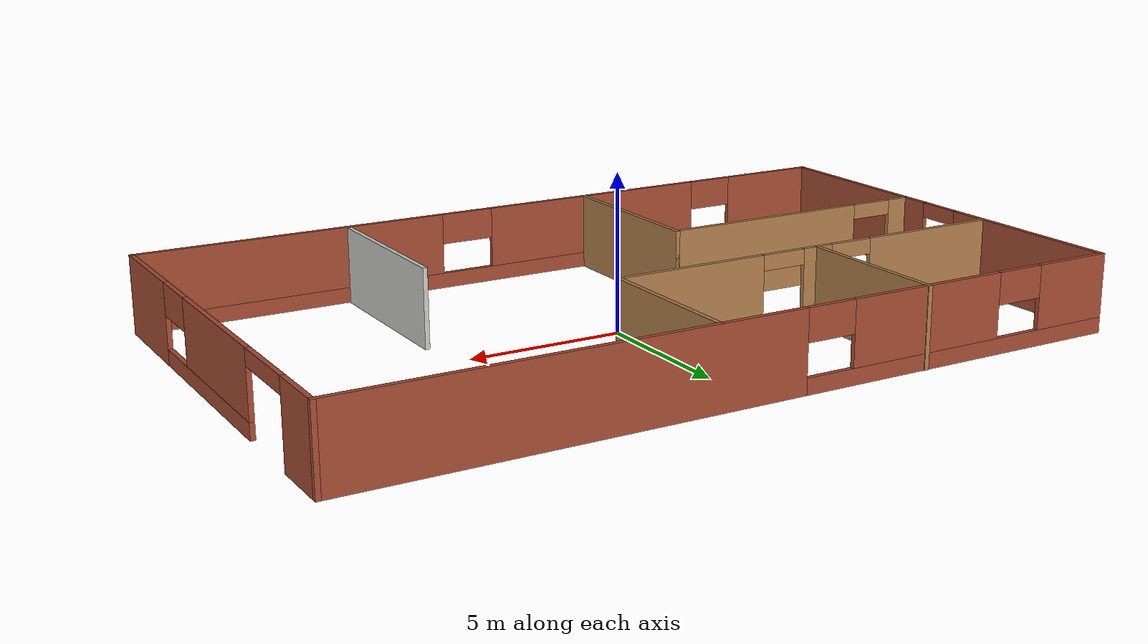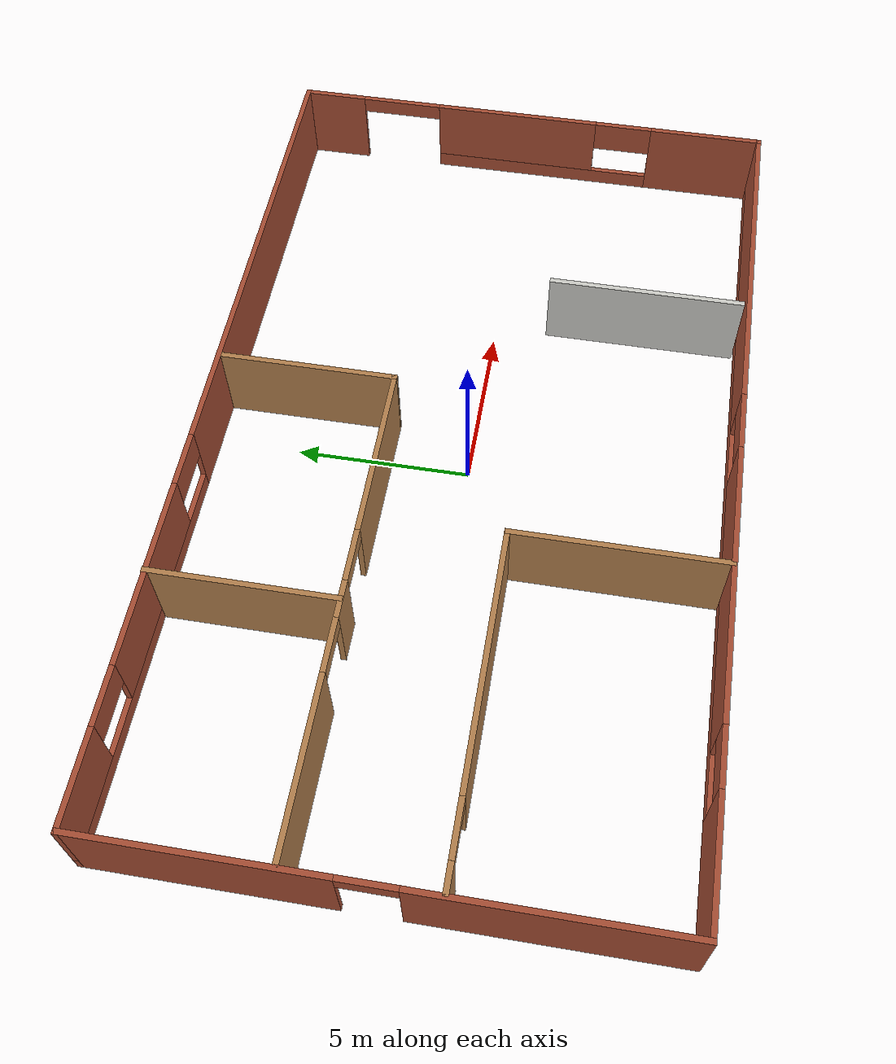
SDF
<?xml version='1.0'?>
<sdf version='1.6'>
  <model name='myhouse'>
    <link name='Wall_1'>
      <pose frame=''>-12.55 -0.012047 0 0 0 -1.5708</pose>
      <self_collide>0</self_collide>
      <kinematic>0</kinematic>
      <visual name='Wall_1_Visual_0'>
        <pose frame=''>-4.24352 0 1.25 0 -0 0</pose>
        <geometry>
          <box>
            <size>6.51297 0.15 2.5</size>
          </box>
        </geometry>
        <material>
          <script>
            <uri>file://media/materials/scripts/gazebo.material</uri>
            <name>Gazebo/Bricks</name>
          </script>
          <ambient>1 1 1 1</ambient>
          <shader type='pixel'/>
          <diffuse>1 1 1 1</diffuse>
          <specular>0.2 0.2 0.2 1</specular>
          <emissive>0 0 0 1</emissive>
        </material>
        <meta>
          <layer>0</layer>
        </meta>
        <transparency>0</transparency>
        <cast_shadows>1</cast_shadows>
      </visual>
      <visual name='Wall_1_Visual_1'>
        <pose frame=''>4.00648 0 1.25 0 -0 0</pose>
        <geometry>
          <box>
            <size>6.98703 0.15 2.5</size>
          </box>
        </geometry>
        <material>
          <script>
            <uri>file://media/materials/scripts/gazebo.material</uri>
            <name>Gazebo/Bricks</name>
          </script>
          <ambient>1 1 1 1</ambient>
          <shader type='pixel'/>
          <diffuse>1 1 1 1</diffuse>
          <specular>0.2 0.2 0.2 1</specular>
          <emissive>0 0 0 1</emissive>
        </material>
        <meta>
          <layer>0</layer>
        </meta>
        <transparency>0</transparency>
        <cast_shadows>1</cast_shadows>
      </visual>
      <visual name='Wall_1_Visual_2'>
        <pose frame=''>-0.237035 0 2.25 0 -0 0</pose>
        <geometry>
          <box>
            <size>1.5 0.15 0.5</size>
          </box>
        </geometry>
        <material>
          <script>
            <uri>file://media/materials/scripts/gazebo.material</uri>
            <name>Gazebo/Bricks</name>
          </script>
          <ambient>1 1 1 1</ambient>
          <shader type='pixel'/>
          <diffuse>1 1 1 1</diffuse>
          <specular>0.2 0.2 0.2 1</specular>
          <emissive>0 0 0 1</emissive>
        </material>
        <meta>
          <layer>0</layer>
        </meta>
        <transparency>0</transparency>
        <cast_shadows>1</cast_shadows>
      </visual>
      <collision name='Wall_1_Collision_0'>
        <laser_retro>0</laser_retro>
        <max_contacts>10</max_contacts>
        <pose frame=''>-4.24352 0 1.25 0 -0 0</pose>
        <geometry>
          <box>
            <size>6.51297 0.15 2.5</size>
          </box>
        </geometry>
        <surface>
          <friction>
            <ode>
              <mu>1</mu>
              <mu2>1</mu2>
              <fdir1>0 0 0</fdir1>
              <slip1>0</slip1>
              <slip2>0</slip2>
            </ode>
            <torsional>
              <coefficient>1</coefficient>
              <patch_radius>0</patch_radius>
              <surface_radius>0</surface_radius>
              <use_patch_radius>1</use_patch_radius>
              <ode>
                <slip>0</slip>
              </ode>
            </torsional>
          </friction>
          <bounce>
            <restitution_coefficient>0</restitution_coefficient>
            <threshold>1e+06</threshold>
          </bounce>
          <contact>
            <collide_without_contact>0</collide_without_contact>
            <collide_without_contact_bitmask>1</collide_without_contact_bitmask>
            <collide_bitmask>1</collide_bitmask>
            <ode>
              <soft_cfm>0</soft_cfm>
              <soft_erp>0.2</soft_erp>
              <kp>1e+13</kp>
              <kd>1</kd>
              <max_vel>0.01</max_vel>
              <min_depth>0</min_depth>
            </ode>
            <bullet>
              <split_impulse>1</split_impulse>
              <split_impulse_penetration_threshold>-0.01</split_impulse_penetration_threshold>
              <soft_cfm>0</soft_cfm>
              <soft_erp>0.2</soft_erp>
              <kp>1e+13</kp>
              <kd>1</kd>
            </bullet>
          </contact>
        </surface>
      </collision>
      <collision name='Wall_1_Collision_1'>
        <laser_retro>0</laser_retro>
        <max_contacts>10</max_contacts>
        <pose frame=''>4.00648 0 1.25 0 -0 0</pose>
        <geometry>
          <box>
            <size>6.98703 0.15 2.5</size>
          </box>
        </geometry>
        <surface>
          <friction>
            <ode>
              <mu>1</mu>
              <mu2>1</mu2>
              <fdir1>0 0 0</fdir1>
              <slip1>0</slip1>
              <slip2>0</slip2>
            </ode>
            <torsional>
              <coefficient>1</coefficient>
              <patch_radius>0</patch_radius>
              <surface_radius>0</surface_radius>
              <use_patch_radius>1</use_patch_radius>
              <ode>
                <slip>0</slip>
              </ode>
            </torsional>
          </friction>
          <bounce>
            <restitution_coefficient>0</restitution_coefficient>
            <threshold>1e+06</threshold>
          </bounce>
          <contact>
            <collide_without_contact>0</collide_without_contact>
            <collide_without_contact_bitmask>1</collide_without_contact_bitmask>
            <collide_bitmask>1</collide_bitmask>
            <ode>
              <soft_cfm>0</soft_cfm>
              <soft_erp>0.2</soft_erp>
              <kp>1e+13</kp>
              <kd>1</kd>
              <max_vel>0.01</max_vel>
              <min_depth>0</min_depth>
            </ode>
            <bullet>
              <split_impulse>1</split_impulse>
              <split_impulse_penetration_threshold>-0.01</split_impulse_penetration_threshold>
              <soft_cfm>0</soft_cfm>
              <soft_erp>0.2</soft_erp>
              <kp>1e+13</kp>
              <kd>1</kd>
            </bullet>
          </contact>
        </surface>
      </collision>
      <collision name='Wall_1_Collision_2'>
        <laser_retro>0</laser_retro>
        <max_contacts>10</max_contacts>
        <pose frame=''>-0.237035 0 2.25 0 -0 0</pose>
        <geometry>
          <box>
            <size>1.5 0.15 0.5</size>
          </box>
        </geometry>
        <surface>
          <friction>
            <ode>
              <mu>1</mu>
              <mu2>1</mu2>
              <fdir1>0 0 0</fdir1>
              <slip1>0</slip1>
              <slip2>0</slip2>
            </ode>
            <torsional>
              <coefficient>1</coefficient>
              <patch_radius>0</patch_radius>
              <surface_radius>0</surface_radius>
              <use_patch_radius>1</use_patch_radius>
              <ode>
                <slip>0</slip>
              </ode>
            </torsional>
          </friction>
          <bounce>
            <restitution_coefficient>0</restitution_coefficient>
            <threshold>1e+06</threshold>
          </bounce>
          <contact>
            <collide_without_contact>0</collide_without_contact>
            <collide_without_contact_bitmask>1</collide_without_contact_bitmask>
            <collide_bitmask>1</collide_bitmask>
            <ode>
              <soft_cfm>0</soft_cfm>
              <soft_erp>0.2</soft_erp>
              <kp>1e+13</kp>
              <kd>1</kd>
              <max_vel>0.01</max_vel>
              <min_depth>0</min_depth>
            </ode>
            <bullet>
              <split_impulse>1</split_impulse>
              <split_impulse_penetration_threshold>-0.01</split_impulse_penetration_threshold>
              <soft_cfm>0</soft_cfm>
              <soft_erp>0.2</soft_erp>
              <kp>1e+13</kp>
              <kd>1</kd>
            </bullet>
          </contact>
        </surface>
      </collision>
    </link>
    <link name='Wall_10'>
      <pose frame=''>-3.11994 -4.47756 0 0 0 -1.5708</pose>
      <self_collide>0</self_collide>
      <kinematic>0</kinematic>
      <visual name='Wall_10_Visual'>
        <pose frame=''>0 0 1.25 0 -0 0</pose>
        <geometry>
          <box>
            <size>6 0.15 2.5</size>
          </box>
        </geometry>
        <material>
          <script>
            <uri>file://media/materials/scripts/gazebo.material</uri>
            <name>Gazebo/Wood</name>
          </script>
          <ambient>0.435294 0.796078 0.67451 1</ambient>
          <shader type='pixel'/>
          <diffuse>1 1 1 1</diffuse>
          <specular>0.2 0.2 0.2 1</specular>
          <emissive>0 0 0 1</emissive>
        </material>
        <meta>
          <layer>0</layer>
        </meta>
        <transparency>0</transparency>
        <cast_shadows>1</cast_shadows>
      </visual>
      <collision name='Wall_10_Collision'>
        <laser_retro>0</laser_retro>
        <max_contacts>10</max_contacts>
        <pose frame=''>0 0 1.25 0 -0 0</pose>
        <geometry>
          <box>
            <size>6 0.15 2.5</size>
          </box>
        </geometry>
        <surface>
          <friction>
            <ode>
              <mu>1</mu>
              <mu2>1</mu2>
              <fdir1>0 0 0</fdir1>
              <slip1>0</slip1>
              <slip2>0</slip2>
            </ode>
            <torsional>
              <coefficient>1</coefficient>
              <patch_radius>0</patch_radius>
              <surface_radius>0</surface_radius>
              <use_patch_radius>1</use_patch_radius>
              <ode>
                <slip>0</slip>
              </ode>
            </torsional>
          </friction>
          <bounce>
            <restitution_coefficient>0</restitution_coefficient>
            <threshold>1e+06</threshold>
          </bounce>
          <contact>
            <collide_without_contact>0</collide_without_contact>
            <collide_without_contact_bitmask>1</collide_without_contact_bitmask>
            <collide_bitmask>1</collide_bitmask>
            <ode>
              <soft_cfm>0</soft_cfm>
              <soft_erp>0.2</soft_erp>
              <kp>1e+13</kp>
              <kd>1</kd>
              <max_vel>0.01</max_vel>
              <min_depth>0</min_depth>
            </ode>
            <bullet>
              <split_impulse>1</split_impulse>
              <split_impulse_penetration_threshold>-0.01</split_impulse_penetration_threshold>
              <soft_cfm>0</soft_cfm>
              <soft_erp>0.2</soft_erp>
              <kp>1e+13</kp>
              <kd>1</kd>
            </bullet>
          </contact>
        </surface>
      </collision>
    </link>
    <link name='Wall_12'>
      <pose frame=''>5.62786 -4.42847 0 0 -0 1.5708</pose>
      <self_collide>0</self_collide>
      <kinematic>0</kinematic>
      <visual name='Wall_12_Visual'>
        <pose frame=''>0 0 1.25 0 -0 0</pose>
        <geometry>
          <box>
            <size>5.75 0.15 2.5</size>
          </box>
        </geometry>
        <material>
          <script>
            <uri>file://media/materials/scripts/gazebo.material</uri>
            <name>Gazebo/CeilingTiled</name>
          </script>
          <ambient>0.333333 1 1 1</ambient>
          <shader type='pixel'/>
          <diffuse>1 1 1 1</diffuse>
          <specular>0 0 0 1</specular>
          <emissive>0 0 0 1</emissive>
        </material>
        <meta>
          <layer>0</layer>
        </meta>
        <transparency>0</transparency>
        <cast_shadows>1</cast_shadows>
      </visual>
      <collision name='Wall_12_Collision'>
        <laser_retro>0</laser_retro>
        <max_contacts>10</max_contacts>
        <pose frame=''>0 0 1.25 0 -0 0</pose>
        <geometry>
          <box>
            <size>5.75 0.15 2.5</size>
          </box>
        </geometry>
        <surface>
          <friction>
            <ode>
              <mu>1</mu>
              <mu2>1</mu2>
              <fdir1>0 0 0</fdir1>
              <slip1>0</slip1>
              <slip2>0</slip2>
            </ode>
            <torsional>
              <coefficient>1</coefficient>
              <patch_radius>0</patch_radius>
              <surface_radius>0</surface_radius>
              <use_patch_radius>1</use_patch_radius>
              <ode>
                <slip>0</slip>
              </ode>
            </torsional>
          </friction>
          <bounce>
            <restitution_coefficient>0</restitution_coefficient>
            <threshold>1e+06</threshold>
          </bounce>
          <contact>
            <collide_without_contact>0</collide_without_contact>
            <collide_without_contact_bitmask>1</collide_without_contact_bitmask>
            <collide_bitmask>1</collide_bitmask>
            <ode>
              <soft_cfm>0</soft_cfm>
              <soft_erp>0.2</soft_erp>
              <kp>1e+13</kp>
              <kd>1</kd>
              <max_vel>0.01</max_vel>
              <min_depth>0</min_depth>
            </ode>
            <bullet>
              <split_impulse>1</split_impulse>
              <split_impulse_penetration_threshold>-0.01</split_impulse_penetration_threshold>
              <soft_cfm>0</soft_cfm>
              <soft_erp>0.2</soft_erp>
              <kp>1e+13</kp>
              <kd>1</kd>
            </bullet>
          </contact>
        </surface>
      </collision>
    </link>
    <link name='Wall_14'>
      <pose frame=''>-5.73434 4.88705 0 0 -0 1.5708</pose>
      <self_collide>0</self_collide>
      <kinematic>0</kinematic>
      <visual name='Wall_14_Visual'>
        <pose frame=''>0 0 1.25 0 -0 0</pose>
        <geometry>
          <box>
            <size>5.25 0.15 2.5</size>
          </box>
        </geometry>
        <material>
          <script>
            <uri>file://media/materials/scripts/gazebo.material</uri>
            <name>Gazebo/Wood</name>
          </script>
          <ambient>1 0 0 1</ambient>
          <shader type='pixel'/>
          <diffuse>1 1 1 1</diffuse>
          <specular>0.2 0.2 0.2 1</specular>
          <emissive>0 0 0 1</emissive>
        </material>
        <meta>
          <layer>0</layer>
        </meta>
        <transparency>0</transparency>
        <cast_shadows>1</cast_shadows>
      </visual>
      <collision name='Wall_14_Collision'>
        <laser_retro>0</laser_retro>
        <max_contacts>10</max_contacts>
        <pose frame=''>0 0 1.25 0 -0 0</pose>
        <geometry>
          <box>
            <size>5.25 0.15 2.5</size>
          </box>
        </geometry>
        <surface>
          <friction>
            <ode>
              <mu>1</mu>
              <mu2>1</mu2>
              <fdir1>0 0 0</fdir1>
              <slip1>0</slip1>
              <slip2>0</slip2>
            </ode>
            <torsional>
              <coefficient>1</coefficient>
              <patch_radius>0</patch_radius>
              <surface_radius>0</surface_radius>
              <use_patch_radius>1</use_patch_radius>
              <ode>
                <slip>0</slip>
              </ode>
            </torsional>
          </friction>
          <bounce>
            <restitution_coefficient>0</restitution_coefficient>
            <threshold>1e+06</threshold>
          </bounce>
          <contact>
            <collide_without_contact>0</collide_without_contact>
            <collide_without_contact_bitmask>1</collide_without_contact_bitmask>
            <collide_bitmask>1</collide_bitmask>
            <ode>
              <soft_cfm>0</soft_cfm>
              <soft_erp>0.2</soft_erp>
              <kp>1e+13</kp>
              <kd>1</kd>
              <max_vel>0.01</max_vel>
              <min_depth>0</min_depth>
            </ode>
            <bullet>
              <split_impulse>1</split_impulse>
              <split_impulse_penetration_threshold>-0.01</split_impulse_penetration_threshold>
              <soft_cfm>0</soft_cfm>
              <soft_erp>0.2</soft_erp>
              <kp>1e+13</kp>
              <kd>1</kd>
            </bullet>
          </contact>
        </surface>
      </collision>
    </link>
    <link name='Wall_2'>
      <pose frame=''>0 -7.43705 0 0 -0 0</pose>
      <self_collide>0</self_collide>
      <kinematic>0</kinematic>
      <visual name='Wall_2_Visual_0'>
        <pose frame=''>-10.8742 0 1.25 0 -0 0</pose>
        <geometry>
          <box>
            <size>3.50151 0.15 2.5</size>
          </box>
        </geometry>
        <material>
          <script>
            <uri>file://media/materials/scripts/gazebo.material</uri>
            <name>Gazebo/Bricks</name>
          </script>
          <ambient>1 1 1 1</ambient>
          <shader type='pixel'/>
          <diffuse>1 1 1 1</diffuse>
          <specular>0.2 0.2 0.2 1</specular>
          <emissive>0 0 0 1</emissive>
        </material>
        <meta>
          <layer>0</layer>
        </meta>
        <transparency>0</transparency>
        <cast_shadows>1</cast_shadows>
      </visual>
      <visual name='Wall_2_Visual_1'>
        <pose frame=''>1.75075 0 0.25 0 -0 0</pose>
        <geometry>
          <box>
            <size>21.7485 0.15 0.5</size>
          </box>
        </geometry>
        <material>
          <script>
            <uri>file://media/materials/scripts/gazebo.material</uri>
            <name>Gazebo/Bricks</name>
          </script>
          <ambient>1 1 1 1</ambient>
          <shader type='pixel'/>
          <diffuse>1 1 1 1</diffuse>
          <specular>0.2 0.2 0.2 1</specular>
          <emissive>0 0 0 1</emissive>
        </material>
        <meta>
          <layer>0</layer>
        </meta>
        <transparency>0</transparency>
        <cast_shadows>1</cast_shadows>
      </visual>
      <visual name='Wall_2_Visual_2'>
        <pose frame=''>-3.49871 0 1.5 0 -0 0</pose>
        <geometry>
          <box>
            <size>8.04956 0.15 2</size>
          </box>
        </geometry>
        <material>
          <script>
            <uri>file://media/materials/scripts/gazebo.material</uri>
            <name>Gazebo/Bricks</name>
          </script>
          <ambient>1 1 1 1</ambient>
          <shader type='pixel'/>
          <diffuse>1 1 1 1</diffuse>
          <specular>0.2 0.2 0.2 1</specular>
          <emissive>0 0 0 1</emissive>
        </material>
        <meta>
          <layer>0</layer>
        </meta>
        <transparency>0</transparency>
        <cast_shadows>1</cast_shadows>
      </visual>
      <visual name='Wall_2_Visual_3'>
        <pose frame=''>7.47553 0 1.5 0 -0 0</pose>
        <geometry>
          <box>
            <size>10.2989 0.15 2</size>
          </box>
        </geometry>
        <material>
          <script>
            <uri>file://media/materials/scripts/gazebo.material</uri>
            <name>Gazebo/Bricks</name>
          </script>
          <ambient>1 1 1 1</ambient>
          <shader type='pixel'/>
          <diffuse>1 1 1 1</diffuse>
          <specular>0.2 0.2 0.2 1</specular>
          <emissive>0 0 0 1</emissive>
        </material>
        <meta>
          <layer>0</layer>
        </meta>
        <transparency>0</transparency>
        <cast_shadows>1</cast_shadows>
      </visual>
      <visual name='Wall_2_Visual_4'>
        <pose frame=''>-8.32349 0 2 0 -0 0</pose>
        <geometry>
          <box>
            <size>1.6 0.15 1</size>
          </box>
        </geometry>
        <material>
          <script>
            <uri>file://media/materials/scripts/gazebo.material</uri>
            <name>Gazebo/Bricks</name>
          </script>
          <ambient>1 1 1 1</ambient>
          <shader type='pixel'/>
          <diffuse>1 1 1 1</diffuse>
          <specular>0.2 0.2 0.2 1</specular>
          <emissive>0 0 0 1</emissive>
        </material>
        <meta>
          <layer>0</layer>
        </meta>
        <transparency>0</transparency>
        <cast_shadows>1</cast_shadows>
      </visual>
      <visual name='Wall_2_Visual_5'>
        <pose frame=''>1.42607 0 2 0 -0 0</pose>
        <geometry>
          <box>
            <size>1.8 0.15 1</size>
          </box>
        </geometry>
        <material>
          <script>
            <uri>file://media/materials/scripts/gazebo.material</uri>
            <name>Gazebo/Bricks</name>
          </script>
          <ambient>1 1 1 1</ambient>
          <shader type='pixel'/>
          <diffuse>1 1 1 1</diffuse>
          <specular>0.2 0.2 0.2 1</specular>
          <emissive>0 0 0 1</emissive>
        </material>
        <meta>
          <layer>0</layer>
        </meta>
        <transparency>0</transparency>
        <cast_shadows>1</cast_shadows>
      </visual>
      <collision name='Wall_2_Collision_0'>
        <laser_retro>0</laser_retro>
        <max_contacts>10</max_contacts>
        <pose frame=''>-10.8742 0 1.25 0 -0 0</pose>
        <geometry>
          <box>
            <size>3.50151 0.15 2.5</size>
          </box>
        </geometry>
        <surface>
          <friction>
            <ode>
              <mu>1</mu>
              <mu2>1</mu2>
              <fdir1>0 0 0</fdir1>
              <slip1>0</slip1>
              <slip2>0</slip2>
            </ode>
            <torsional>
              <coefficient>1</coefficient>
              <patch_radius>0</patch_radius>
              <surface_radius>0</surface_radius>
              <use_patch_radius>1</use_patch_radius>
              <ode>
                <slip>0</slip>
              </ode>
            </torsional>
          </friction>
          <bounce>
            <restitution_coefficient>0</restitution_coefficient>
            <threshold>1e+06</threshold>
          </bounce>
          <contact>
            <collide_without_contact>0</collide_without_contact>
            <collide_without_contact_bitmask>1</collide_without_contact_bitmask>
            <collide_bitmask>1</collide_bitmask>
            <ode>
              <soft_cfm>0</soft_cfm>
              <soft_erp>0.2</soft_erp>
              <kp>1e+13</kp>
              <kd>1</kd>
              <max_vel>0.01</max_vel>
              <min_depth>0</min_depth>
            </ode>
            <bullet>
              <split_impulse>1</split_impulse>
              <split_impulse_penetration_threshold>-0.01</split_impulse_penetration_threshold>
              <soft_cfm>0</soft_cfm>
              <soft_erp>0.2</soft_erp>
              <kp>1e+13</kp>
              <kd>1</kd>
            </bullet>
          </contact>
        </surface>
      </collision>
      <collision name='Wall_2_Collision_1'>
        <laser_retro>0</laser_retro>
        <max_contacts>10</max_contacts>
        <pose frame=''>1.75075 0 0.25 0 -0 0</pose>
        <geometry>
          <box>
            <size>21.7485 0.15 0.5</size>
          </box>
        </geometry>
        <surface>
          <friction>
            <ode>
              <mu>1</mu>
              <mu2>1</mu2>
              <fdir1>0 0 0</fdir1>
              <slip1>0</slip1>
              <slip2>0</slip2>
            </ode>
            <torsional>
              <coefficient>1</coefficient>
              <patch_radius>0</patch_radius>
              <surface_radius>0</surface_radius>
              <use_patch_radius>1</use_patch_radius>
              <ode>
                <slip>0</slip>
              </ode>
            </torsional>
          </friction>
          <bounce>
            <restitution_coefficient>0</restitution_coefficient>
            <threshold>1e+06</threshold>
          </bounce>
          <contact>
            <collide_without_contact>0</collide_without_contact>
            <collide_without_contact_bitmask>1</collide_without_contact_bitmask>
            <collide_bitmask>1</collide_bitmask>
            <ode>
              <soft_cfm>0</soft_cfm>
              <soft_erp>0.2</soft_erp>
              <kp>1e+13</kp>
              <kd>1</kd>
              <max_vel>0.01</max_vel>
              <min_depth>0</min_depth>
            </ode>
            <bullet>
              <split_impulse>1</split_impulse>
              <split_impulse_penetration_threshold>-0.01</split_impulse_penetration_threshold>
              <soft_cfm>0</soft_cfm>
              <soft_erp>0.2</soft_erp>
              <kp>1e+13</kp>
              <kd>1</kd>
            </bullet>
          </contact>
        </surface>
      </collision>
      <collision name='Wall_2_Collision_2'>
        <laser_retro>0</laser_retro>
        <max_contacts>10</max_contacts>
        <pose frame=''>-3.49871 0 1.5 0 -0 0</pose>
        <geometry>
          <box>
            <size>8.04956 0.15 2</size>
          </box>
        </geometry>
        <surface>
          <friction>
            <ode>
              <mu>1</mu>
              <mu2>1</mu2>
              <fdir1>0 0 0</fdir1>
              <slip1>0</slip1>
              <slip2>0</slip2>
            </ode>
            <torsional>
              <coefficient>1</coefficient>
              <patch_radius>0</patch_radius>
              <surface_radius>0</surface_radius>
              <use_patch_radius>1</use_patch_radius>
              <ode>
                <slip>0</slip>
              </ode>
            </torsional>
          </friction>
          <bounce>
            <restitution_coefficient>0</restitution_coefficient>
            <threshold>1e+06</threshold>
          </bounce>
          <contact>
            <collide_without_contact>0</collide_without_contact>
            <collide_without_contact_bitmask>1</collide_without_contact_bitmask>
            <collide_bitmask>1</collide_bitmask>
            <ode>
              <soft_cfm>0</soft_cfm>
              <soft_erp>0.2</soft_erp>
              <kp>1e+13</kp>
              <kd>1</kd>
              <max_vel>0.01</max_vel>
              <min_depth>0</min_depth>
            </ode>
            <bullet>
              <split_impulse>1</split_impulse>
              <split_impulse_penetration_threshold>-0.01</split_impulse_penetration_threshold>
              <soft_cfm>0</soft_cfm>
              <soft_erp>0.2</soft_erp>
              <kp>1e+13</kp>
              <kd>1</kd>
            </bullet>
          </contact>
        </surface>
      </collision>
      <collision name='Wall_2_Collision_3'>
        <laser_retro>0</laser_retro>
        <max_contacts>10</max_contacts>
        <pose frame=''>7.47553 0 1.5 0 -0 0</pose>
        <geometry>
          <box>
            <size>10.2989 0.15 2</size>
          </box>
        </geometry>
        <surface>
          <friction>
            <ode>
              <mu>1</mu>
              <mu2>1</mu2>
              <fdir1>0 0 0</fdir1>
              <slip1>0</slip1>
              <slip2>0</slip2>
            </ode>
            <torsional>
              <coefficient>1</coefficient>
              <patch_radius>0</patch_radius>
              <surface_radius>0</surface_radius>
              <use_patch_radius>1</use_patch_radius>
              <ode>
                <slip>0</slip>
              </ode>
            </torsional>
          </friction>
          <bounce>
            <restitution_coefficient>0</restitution_coefficient>
            <threshold>1e+06</threshold>
          </bounce>
          <contact>
            <collide_without_contact>0</collide_without_contact>
            <collide_without_contact_bitmask>1</collide_without_contact_bitmask>
            <collide_bitmask>1</collide_bitmask>
            <ode>
              <soft_cfm>0</soft_cfm>
              <soft_erp>0.2</soft_erp>
              <kp>1e+13</kp>
              <kd>1</kd>
              <max_vel>0.01</max_vel>
              <min_depth>0</min_depth>
            </ode>
            <bullet>
              <split_impulse>1</split_impulse>
              <split_impulse_penetration_threshold>-0.01</split_impulse_penetration_threshold>
              <soft_cfm>0</soft_cfm>
              <soft_erp>0.2</soft_erp>
              <kp>1e+13</kp>
              <kd>1</kd>
            </bullet>
          </contact>
        </surface>
      </collision>
      <collision name='Wall_2_Collision_5'>
        <laser_retro>0</laser_retro>
        <max_contacts>10</max_contacts>
        <pose frame=''>1.42607 0 2 0 -0 0</pose>
        <geometry>
          <box>
            <size>1.8 0.15 1</size>
          </box>
        </geometry>
        <surface>
          <friction>
            <ode>
              <mu>1</mu>
              <mu2>1</mu2>
              <fdir1>0 0 0</fdir1>
              <slip1>0</slip1>
              <slip2>0</slip2>
            </ode>
            <torsional>
              <coefficient>1</coefficient>
              <patch_radius>0</patch_radius>
              <surface_radius>0</surface_radius>
              <use_patch_radius>1</use_patch_radius>
              <ode>
                <slip>0</slip>
              </ode>
            </torsional>
          </friction>
          <bounce>
            <restitution_coefficient>0</restitution_coefficient>
            <threshold>1e+06</threshold>
          </bounce>
          <contact>
            <collide_without_contact>0</collide_without_contact>
            <collide_without_contact_bitmask>1</collide_without_contact_bitmask>
            <collide_bitmask>1</collide_bitmask>
            <ode>
              <soft_cfm>0</soft_cfm>
              <soft_erp>0.2</soft_erp>
              <kp>1e+13</kp>
              <kd>1</kd>
              <max_vel>0.01</max_vel>
              <min_depth>0</min_depth>
            </ode>
            <bullet>
              <split_impulse>1</split_impulse>
              <split_impulse_penetration_threshold>-0.01</split_impulse_penetration_threshold>
              <soft_cfm>0</soft_cfm>
              <soft_erp>0.2</soft_erp>
              <kp>1e+13</kp>
              <kd>1</kd>
            </bullet>
          </contact>
        </surface>
      </collision>
      <collision name='Wall_2_Collision_4'>
        <laser_retro>0</laser_retro>
        <max_contacts>10</max_contacts>
        <pose frame=''>-8.32349 0 2 0 -0 0</pose>
        <geometry>
          <box>
            <size>1.6 0.15 1</size>
          </box>
        </geometry>
        <surface>
          <friction>
            <ode>
              <mu>1</mu>
              <mu2>1</mu2>
              <fdir1>0 0 0</fdir1>
              <slip1>0</slip1>
              <slip2>0</slip2>
            </ode>
            <torsional>
              <coefficient>1</coefficient>
              <patch_radius>0</patch_radius>
              <surface_radius>0</surface_radius>
              <use_patch_radius>1</use_patch_radius>
              <ode>
                <slip>0</slip>
              </ode>
            </torsional>
          </friction>
          <bounce>
            <restitution_coefficient>0</restitution_coefficient>
            <threshold>1e+06</threshold>
          </bounce>
          <contact>
            <collide_without_contact>0</collide_without_contact>
            <collide_without_contact_bitmask>1</collide_without_contact_bitmask>
            <collide_bitmask>1</collide_bitmask>
            <ode>
              <soft_cfm>0</soft_cfm>
              <soft_erp>0.2</soft_erp>
              <kp>1e+13</kp>
              <kd>1</kd>
              <max_vel>0.01</max_vel>
              <min_depth>0</min_depth>
            </ode>
            <bullet>
              <split_impulse>1</split_impulse>
              <split_impulse_penetration_threshold>-0.01</split_impulse_penetration_threshold>
              <soft_cfm>0</soft_cfm>
              <soft_erp>0.2</soft_erp>
              <kp>1e+13</kp>
              <kd>1</kd>
            </bullet>
          </contact>
        </surface>
      </collision>
    </link>
    <link name='Wall_3'>
      <pose frame=''>12.55 -0.012047 0 0 -0 1.5708</pose>
      <self_collide>0</self_collide>
      <kinematic>0</kinematic>
      <visual name='Wall_3_Visual_0'>
        <pose frame=''>-5.73076 0 1.25 0 -0 0</pose>
        <geometry>
          <box>
            <size>3.53847 0.15 2.5</size>
          </box>
        </geometry>
        <material>
          <script>
            <uri>file://media/materials/scripts/gazebo.material</uri>
            <name>Gazebo/Bricks</name>
          </script>
          <ambient>1 1 1 1</ambient>
          <shader type='pixel'/>
          <diffuse>1 1 1 1</diffuse>
          <specular>0.2 0.2 0.2 1</specular>
          <emissive>0 0 0 1</emissive>
        </material>
        <meta>
          <layer>0</layer>
        </meta>
        <transparency>0</transparency>
        <cast_shadows>1</cast_shadows>
      </visual>
      <visual name='Wall_3_Visual_1'>
        <pose frame=''>6.50526 0 1.25 0 -0 0</pose>
        <geometry>
          <box>
            <size>1.98949 0.15 2.5</size>
          </box>
        </geometry>
        <material>
          <script>
            <uri>file://media/materials/scripts/gazebo.material</uri>
            <name>Gazebo/Bricks</name>
          </script>
          <ambient>1 1 1 1</ambient>
          <shader type='pixel'/>
          <diffuse>1 1 1 1</diffuse>
          <specular>0.2 0.2 0.2 1</specular>
          <emissive>0 0 0 1</emissive>
        </material>
        <meta>
          <layer>0</layer>
        </meta>
        <transparency>0</transparency>
        <cast_shadows>1</cast_shadows>
      </visual>
      <visual name='Wall_3_Visual_2'>
        <pose frame=''>-0.475509 0 0.25 0 -0 0</pose>
        <geometry>
          <box>
            <size>6.97204 0.15 0.5</size>
          </box>
        </geometry>
        <material>
          <script>
            <uri>file://media/materials/scripts/gazebo.material</uri>
            <name>Gazebo/Bricks</name>
          </script>
          <ambient>1 1 1 1</ambient>
          <shader type='pixel'/>
          <diffuse>1 1 1 1</diffuse>
          <specular>0.2 0.2 0.2 1</specular>
          <emissive>0 0 0 1</emissive>
        </material>
        <meta>
          <layer>0</layer>
        </meta>
        <transparency>0</transparency>
        <cast_shadows>1</cast_shadows>
      </visual>
      <visual name='Wall_3_Visual_3'>
        <pose frame=''>0.424491 0 1.5 0 -0 0</pose>
        <geometry>
          <box>
            <size>5.17204 0.15 2</size>
          </box>
        </geometry>
        <material>
          <script>
            <uri>file://media/materials/scripts/gazebo.material</uri>
            <name>Gazebo/Bricks</name>
          </script>
          <ambient>1 1 1 1</ambient>
          <shader type='pixel'/>
          <diffuse>1 1 1 1</diffuse>
          <specular>0.2 0.2 0.2 1</specular>
          <emissive>0 0 0 1</emissive>
        </material>
        <meta>
          <layer>0</layer>
        </meta>
        <transparency>0</transparency>
        <cast_shadows>1</cast_shadows>
      </visual>
      <visual name='Wall_3_Visual_4'>
        <pose frame=''>-3.06153 0 2 0 -0 0</pose>
        <geometry>
          <box>
            <size>1.8 0.15 1</size>
          </box>
        </geometry>
        <material>
          <script>
            <uri>file://media/materials/scripts/gazebo.material</uri>
            <name>Gazebo/Bricks</name>
          </script>
          <ambient>1 1 1 1</ambient>
          <shader type='pixel'/>
          <diffuse>1 1 1 1</diffuse>
          <specular>0.2 0.2 0.2 1</specular>
          <emissive>0 0 0 1</emissive>
        </material>
        <meta>
          <layer>0</layer>
        </meta>
        <transparency>0</transparency>
        <cast_shadows>1</cast_shadows>
      </visual>
      <visual name='Wall_3_Visual_5'>
        <pose frame=''>4.26051 0 2.25 0 -0 0</pose>
        <geometry>
          <box>
            <size>2.5 0.15 0.5</size>
          </box>
        </geometry>
        <material>
          <script>
            <uri>file://media/materials/scripts/gazebo.material</uri>
            <name>Gazebo/Bricks</name>
          </script>
          <ambient>1 1 1 1</ambient>
          <shader type='pixel'/>
          <diffuse>1 1 1 1</diffuse>
          <specular>0.2 0.2 0.2 1</specular>
          <emissive>0 0 0 1</emissive>
        </material>
        <meta>
          <layer>0</layer>
        </meta>
        <transparency>0</transparency>
        <cast_shadows>1</cast_shadows>
      </visual>
      <collision name='Wall_3_Collision_0'>
        <laser_retro>0</laser_retro>
        <max_contacts>10</max_contacts>
        <pose frame=''>-5.73076 0 1.25 0 -0 0</pose>
        <geometry>
          <box>
            <size>3.53847 0.15 2.5</size>
          </box>
        </geometry>
        <surface>
          <friction>
            <ode>
              <mu>1</mu>
              <mu2>1</mu2>
              <fdir1>0 0 0</fdir1>
              <slip1>0</slip1>
              <slip2>0</slip2>
            </ode>
            <torsional>
              <coefficient>1</coefficient>
              <patch_radius>0</patch_radius>
              <surface_radius>0</surface_radius>
              <use_patch_radius>1</use_patch_radius>
              <ode>
                <slip>0</slip>
              </ode>
            </torsional>
          </friction>
          <bounce>
            <restitution_coefficient>0</restitution_coefficient>
            <threshold>1e+06</threshold>
          </bounce>
          <contact>
            <collide_without_contact>0</collide_without_contact>
            <collide_without_contact_bitmask>1</collide_without_contact_bitmask>
            <collide_bitmask>1</collide_bitmask>
            <ode>
              <soft_cfm>0</soft_cfm>
              <soft_erp>0.2</soft_erp>
              <kp>1e+13</kp>
              <kd>1</kd>
              <max_vel>0.01</max_vel>
              <min_depth>0</min_depth>
            </ode>
            <bullet>
              <split_impulse>1</split_impulse>
              <split_impulse_penetration_threshold>-0.01</split_impulse_penetration_threshold>
              <soft_cfm>0</soft_cfm>
              <soft_erp>0.2</soft_erp>
              <kp>1e+13</kp>
              <kd>1</kd>
            </bullet>
          </contact>
        </surface>
      </collision>
      <collision name='Wall_3_Collision_1'>
        <laser_retro>0</laser_retro>
        <max_contacts>10</max_contacts>
        <pose frame=''>6.50526 0 1.25 0 -0 0</pose>
        <geometry>
          <box>
            <size>1.98949 0.15 2.5</size>
          </box>
        </geometry>
        <surface>
          <friction>
            <ode>
              <mu>1</mu>
              <mu2>1</mu2>
              <fdir1>0 0 0</fdir1>
              <slip1>0</slip1>
              <slip2>0</slip2>
            </ode>
            <torsional>
              <coefficient>1</coefficient>
              <patch_radius>0</patch_radius>
              <surface_radius>0</surface_radius>
              <use_patch_radius>1</use_patch_radius>
              <ode>
                <slip>0</slip>
              </ode>
            </torsional>
          </friction>
          <bounce>
            <restitution_coefficient>0</restitution_coefficient>
            <threshold>1e+06</threshold>
          </bounce>
          <contact>
            <collide_without_contact>0</collide_without_contact>
            <collide_without_contact_bitmask>1</collide_without_contact_bitmask>
            <collide_bitmask>1</collide_bitmask>
            <ode>
              <soft_cfm>0</soft_cfm>
              <soft_erp>0.2</soft_erp>
              <kp>1e+13</kp>
              <kd>1</kd>
              <max_vel>0.01</max_vel>
              <min_depth>0</min_depth>
            </ode>
            <bullet>
              <split_impulse>1</split_impulse>
              <split_impulse_penetration_threshold>-0.01</split_impulse_penetration_threshold>
              <soft_cfm>0</soft_cfm>
              <soft_erp>0.2</soft_erp>
              <kp>1e+13</kp>
              <kd>1</kd>
            </bullet>
          </contact>
        </surface>
      </collision>
      <collision name='Wall_3_Collision_2'>
        <laser_retro>0</laser_retro>
        <max_contacts>10</max_contacts>
        <pose frame=''>-0.475509 0 0.25 0 -0 0</pose>
        <geometry>
          <box>
            <size>6.97204 0.15 0.5</size>
          </box>
        </geometry>
        <surface>
          <friction>
            <ode>
              <mu>1</mu>
              <mu2>1</mu2>
              <fdir1>0 0 0</fdir1>
              <slip1>0</slip1>
              <slip2>0</slip2>
            </ode>
            <torsional>
              <coefficient>1</coefficient>
              <patch_radius>0</patch_radius>
              <surface_radius>0</surface_radius>
              <use_patch_radius>1</use_patch_radius>
              <ode>
                <slip>0</slip>
              </ode>
            </torsional>
          </friction>
          <bounce>
            <restitution_coefficient>0</restitution_coefficient>
            <threshold>1e+06</threshold>
          </bounce>
          <contact>
            <collide_without_contact>0</collide_without_contact>
            <collide_without_contact_bitmask>1</collide_without_contact_bitmask>
            <collide_bitmask>1</collide_bitmask>
            <ode>
              <soft_cfm>0</soft_cfm>
              <soft_erp>0.2</soft_erp>
              <kp>1e+13</kp>
              <kd>1</kd>
              <max_vel>0.01</max_vel>
              <min_depth>0</min_depth>
            </ode>
            <bullet>
              <split_impulse>1</split_impulse>
              <split_impulse_penetration_threshold>-0.01</split_impulse_penetration_threshold>
              <soft_cfm>0</soft_cfm>
              <soft_erp>0.2</soft_erp>
              <kp>1e+13</kp>
              <kd>1</kd>
            </bullet>
          </contact>
        </surface>
      </collision>
      <collision name='Wall_3_Collision_3'>
        <laser_retro>0</laser_retro>
        <max_contacts>10</max_contacts>
        <pose frame=''>0.424491 0 1.5 0 -0 0</pose>
        <geometry>
          <box>
            <size>5.17204 0.15 2</size>
          </box>
        </geometry>
        <surface>
          <friction>
            <ode>
              <mu>1</mu>
              <mu2>1</mu2>
              <fdir1>0 0 0</fdir1>
              <slip1>0</slip1>
              <slip2>0</slip2>
            </ode>
            <torsional>
              <coefficient>1</coefficient>
              <patch_radius>0</patch_radius>
              <surface_radius>0</surface_radius>
              <use_patch_radius>1</use_patch_radius>
              <ode>
                <slip>0</slip>
              </ode>
            </torsional>
          </friction>
          <bounce>
            <restitution_coefficient>0</restitution_coefficient>
            <threshold>1e+06</threshold>
          </bounce>
          <contact>
            <collide_without_contact>0</collide_without_contact>
            <collide_without_contact_bitmask>1</collide_without_contact_bitmask>
            <collide_bitmask>1</collide_bitmask>
            <ode>
              <soft_cfm>0</soft_cfm>
              <soft_erp>0.2</soft_erp>
              <kp>1e+13</kp>
              <kd>1</kd>
              <max_vel>0.01</max_vel>
              <min_depth>0</min_depth>
            </ode>
            <bullet>
              <split_impulse>1</split_impulse>
              <split_impulse_penetration_threshold>-0.01</split_impulse_penetration_threshold>
              <soft_cfm>0</soft_cfm>
              <soft_erp>0.2</soft_erp>
              <kp>1e+13</kp>
              <kd>1</kd>
            </bullet>
          </contact>
        </surface>
      </collision>
      <collision name='Wall_3_Collision_5'>
        <laser_retro>0</laser_retro>
        <max_contacts>10</max_contacts>
        <pose frame=''>4.26051 0 2.25 0 -0 0</pose>
        <geometry>
          <box>
            <size>2.5 0.15 0.5</size>
          </box>
        </geometry>
        <surface>
          <friction>
            <ode>
              <mu>1</mu>
              <mu2>1</mu2>
              <fdir1>0 0 0</fdir1>
              <slip1>0</slip1>
              <slip2>0</slip2>
            </ode>
            <torsional>
              <coefficient>1</coefficient>
              <patch_radius>0</patch_radius>
              <surface_radius>0</surface_radius>
              <use_patch_radius>1</use_patch_radius>
              <ode>
                <slip>0</slip>
              </ode>
            </torsional>
          </friction>
          <bounce>
            <restitution_coefficient>0</restitution_coefficient>
            <threshold>1e+06</threshold>
          </bounce>
          <contact>
            <collide_without_contact>0</collide_without_contact>
            <collide_without_contact_bitmask>1</collide_without_contact_bitmask>
            <collide_bitmask>1</collide_bitmask>
            <ode>
              <soft_cfm>0</soft_cfm>
              <soft_erp>0.2</soft_erp>
              <kp>1e+13</kp>
              <kd>1</kd>
              <max_vel>0.01</max_vel>
              <min_depth>0</min_depth>
            </ode>
            <bullet>
              <split_impulse>1</split_impulse>
              <split_impulse_penetration_threshold>-0.01</split_impulse_penetration_threshold>
              <soft_cfm>0</soft_cfm>
              <soft_erp>0.2</soft_erp>
              <kp>1e+13</kp>
              <kd>1</kd>
            </bullet>
          </contact>
        </surface>
      </collision>
      <collision name='Wall_3_Collision_4'>
        <laser_retro>0</laser_retro>
        <max_contacts>10</max_contacts>
        <pose frame=''>-3.06153 0 2 0 -0 0</pose>
        <geometry>
          <box>
            <size>1.8 0.15 1</size>
          </box>
        </geometry>
        <surface>
          <friction>
            <ode>
              <mu>1</mu>
              <mu2>1</mu2>
              <fdir1>0 0 0</fdir1>
              <slip1>0</slip1>
              <slip2>0</slip2>
            </ode>
            <torsional>
              <coefficient>1</coefficient>
              <patch_radius>0</patch_radius>
              <surface_radius>0</surface_radius>
              <use_patch_radius>1</use_patch_radius>
              <ode>
                <slip>0</slip>
              </ode>
            </torsional>
          </friction>
          <bounce>
            <restitution_coefficient>0</restitution_coefficient>
            <threshold>1e+06</threshold>
          </bounce>
          <contact>
            <collide_without_contact>0</collide_without_contact>
            <collide_without_contact_bitmask>1</collide_without_contact_bitmask>
            <collide_bitmask>1</collide_bitmask>
            <ode>
              <soft_cfm>0</soft_cfm>
              <soft_erp>0.2</soft_erp>
              <kp>1e+13</kp>
              <kd>1</kd>
              <max_vel>0.01</max_vel>
              <min_depth>0</min_depth>
            </ode>
            <bullet>
              <split_impulse>1</split_impulse>
              <split_impulse_penetration_threshold>-0.01</split_impulse_penetration_threshold>
              <soft_cfm>0</soft_cfm>
              <soft_erp>0.2</soft_erp>
              <kp>1e+13</kp>
              <kd>1</kd>
            </bullet>
          </contact>
        </surface>
      </collision>
    </link>
    <link name='Wall_4'>
      <pose frame=''>0 7.41295 0 0 -0 3.14159</pose>
      <self_collide>0</self_collide>
      <kinematic>0</kinematic>
      <visual name='Wall_4_Visual_0'>
        <pose frame=''>-5.56469 0 1.25 0 -0 0</pose>
        <geometry>
          <box>
            <size>14.1206 0.15 2.5</size>
          </box>
        </geometry>
        <material>
          <script>
            <uri>file://media/materials/scripts/gazebo.material</uri>
            <name>Gazebo/Bricks</name>
          </script>
          <ambient>1 1 1 1</ambient>
          <shader type='pixel'/>
          <diffuse>1 1 1 1</diffuse>
          <specular>0.2 0.2 0.2 1</specular>
          <emissive>0 0 0 1</emissive>
        </material>
        <meta>
          <layer>0</layer>
        </meta>
        <transparency>0</transparency>
        <cast_shadows>1</cast_shadows>
      </visual>
      <visual name='Wall_4_Visual_1'>
        <pose frame=''>7.06031 0 0.25 0 -0 0</pose>
        <geometry>
          <box>
            <size>11.1294 0.15 0.5</size>
          </box>
        </geometry>
        <material>
          <script>
            <uri>file://media/materials/scripts/gazebo.material</uri>
            <name>Gazebo/Bricks</name>
          </script>
          <ambient>1 1 1 1</ambient>
          <shader type='pixel'/>
          <diffuse>1 1 1 1</diffuse>
          <specular>0.2 0.2 0.2 1</specular>
          <emissive>0 0 0 1</emissive>
        </material>
        <meta>
          <layer>0</layer>
        </meta>
        <transparency>0</transparency>
        <cast_shadows>1</cast_shadows>
      </visual>
      <visual name='Wall_4_Visual_2'>
        <pose frame=''>5.75457 0 1.5 0 -0 0</pose>
        <geometry>
          <box>
            <size>5.3179 0.15 2</size>
          </box>
        </geometry>
        <material>
          <script>
            <uri>file://media/materials/scripts/gazebo.material</uri>
            <name>Gazebo/Bricks</name>
          </script>
          <ambient>1 1 1 1</ambient>
          <shader type='pixel'/>
          <diffuse>1 1 1 1</diffuse>
          <specular>0.2 0.2 0.2 1</specular>
          <emissive>0 0 0 1</emissive>
        </material>
        <meta>
          <layer>0</layer>
        </meta>
        <transparency>0</transparency>
        <cast_shadows>1</cast_shadows>
      </visual>
      <visual name='Wall_4_Visual_3'>
        <pose frame=''>11.3193 0 1.5 0 -0 0</pose>
        <geometry>
          <box>
            <size>2.61148 0.15 2</size>
          </box>
        </geometry>
        <material>
          <script>
            <uri>file://media/materials/scripts/gazebo.material</uri>
            <name>Gazebo/Bricks</name>
          </script>
          <ambient>1 1 1 1</ambient>
          <shader type='pixel'/>
          <diffuse>1 1 1 1</diffuse>
          <specular>0.2 0.2 0.2 1</specular>
          <emissive>0 0 0 1</emissive>
        </material>
        <meta>
          <layer>0</layer>
        </meta>
        <transparency>0</transparency>
        <cast_shadows>1</cast_shadows>
      </visual>
      <visual name='Wall_4_Visual_4'>
        <pose frame=''>2.29561 0 2 0 -0 0</pose>
        <geometry>
          <box>
            <size>1.6 0.15 1</size>
          </box>
        </geometry>
        <material>
          <script>
            <uri>file://media/materials/scripts/gazebo.material</uri>
            <name>Gazebo/Bricks</name>
          </script>
          <ambient>1 1 1 1</ambient>
          <shader type='pixel'/>
          <diffuse>1 1 1 1</diffuse>
          <specular>0.2 0.2 0.2 1</specular>
          <emissive>0 0 0 1</emissive>
        </material>
        <meta>
          <layer>0</layer>
        </meta>
        <transparency>0</transparency>
        <cast_shadows>1</cast_shadows>
      </visual>
      <visual name='Wall_4_Visual_5'>
        <pose frame=''>9.21352 0 2 0 -0 0</pose>
        <geometry>
          <box>
            <size>1.6 0.15 1</size>
          </box>
        </geometry>
        <material>
          <script>
            <uri>file://media/materials/scripts/gazebo.material</uri>
            <name>Gazebo/Bricks</name>
          </script>
          <ambient>1 1 1 1</ambient>
          <shader type='pixel'/>
          <diffuse>1 1 1 1</diffuse>
          <specular>0.2 0.2 0.2 1</specular>
          <emissive>0 0 0 1</emissive>
        </material>
        <meta>
          <layer>0</layer>
        </meta>
        <transparency>0</transparency>
        <cast_shadows>1</cast_shadows>
      </visual>
      <collision name='Wall_4_Collision_0'>
        <laser_retro>0</laser_retro>
        <max_contacts>10</max_contacts>
        <pose frame=''>-5.56469 0 1.25 0 -0 0</pose>
        <geometry>
          <box>
            <size>14.1206 0.15 2.5</size>
          </box>
        </geometry>
        <surface>
          <friction>
            <ode>
              <mu>1</mu>
              <mu2>1</mu2>
              <fdir1>0 0 0</fdir1>
              <slip1>0</slip1>
              <slip2>0</slip2>
            </ode>
            <torsional>
              <coefficient>1</coefficient>
              <patch_radius>0</patch_radius>
              <surface_radius>0</surface_radius>
              <use_patch_radius>1</use_patch_radius>
              <ode>
                <slip>0</slip>
              </ode>
            </torsional>
          </friction>
          <bounce>
            <restitution_coefficient>0</restitution_coefficient>
            <threshold>1e+06</threshold>
          </bounce>
          <contact>
            <collide_without_contact>0</collide_without_contact>
            <collide_without_contact_bitmask>1</collide_without_contact_bitmask>
            <collide_bitmask>1</collide_bitmask>
            <ode>
              <soft_cfm>0</soft_cfm>
              <soft_erp>0.2</soft_erp>
              <kp>1e+13</kp>
              <kd>1</kd>
              <max_vel>0.01</max_vel>
              <min_depth>0</min_depth>
            </ode>
            <bullet>
              <split_impulse>1</split_impulse>
              <split_impulse_penetration_threshold>-0.01</split_impulse_penetration_threshold>
              <soft_cfm>0</soft_cfm>
              <soft_erp>0.2</soft_erp>
              <kp>1e+13</kp>
              <kd>1</kd>
            </bullet>
          </contact>
        </surface>
      </collision>
      <collision name='Wall_4_Collision_1'>
        <laser_retro>0</laser_retro>
        <max_contacts>10</max_contacts>
        <pose frame=''>7.06031 0 0.25 0 -0 0</pose>
        <geometry>
          <box>
            <size>11.1294 0.15 0.5</size>
          </box>
        </geometry>
        <surface>
          <friction>
            <ode>
              <mu>1</mu>
              <mu2>1</mu2>
              <fdir1>0 0 0</fdir1>
              <slip1>0</slip1>
              <slip2>0</slip2>
            </ode>
            <torsional>
              <coefficient>1</coefficient>
              <patch_radius>0</patch_radius>
              <surface_radius>0</surface_radius>
              <use_patch_radius>1</use_patch_radius>
              <ode>
                <slip>0</slip>
              </ode>
            </torsional>
          </friction>
          <bounce>
            <restitution_coefficient>0</restitution_coefficient>
            <threshold>1e+06</threshold>
          </bounce>
          <contact>
            <collide_without_contact>0</collide_without_contact>
            <collide_without_contact_bitmask>1</collide_without_contact_bitmask>
            <collide_bitmask>1</collide_bitmask>
            <ode>
              <soft_cfm>0</soft_cfm>
              <soft_erp>0.2</soft_erp>
              <kp>1e+13</kp>
              <kd>1</kd>
              <max_vel>0.01</max_vel>
              <min_depth>0</min_depth>
            </ode>
            <bullet>
              <split_impulse>1</split_impulse>
              <split_impulse_penetration_threshold>-0.01</split_impulse_penetration_threshold>
              <soft_cfm>0</soft_cfm>
              <soft_erp>0.2</soft_erp>
              <kp>1e+13</kp>
              <kd>1</kd>
            </bullet>
          </contact>
        </surface>
      </collision>
      <collision name='Wall_4_Collision_2'>
        <laser_retro>0</laser_retro>
        <max_contacts>10</max_contacts>
        <pose frame=''>5.75457 0 1.5 0 -0 0</pose>
        <geometry>
          <box>
            <size>5.3179 0.15 2</size>
          </box>
        </geometry>
        <surface>
          <friction>
            <ode>
              <mu>1</mu>
              <mu2>1</mu2>
              <fdir1>0 0 0</fdir1>
              <slip1>0</slip1>
              <slip2>0</slip2>
            </ode>
            <torsional>
              <coefficient>1</coefficient>
              <patch_radius>0</patch_radius>
              <surface_radius>0</surface_radius>
              <use_patch_radius>1</use_patch_radius>
              <ode>
                <slip>0</slip>
              </ode>
            </torsional>
          </friction>
          <bounce>
            <restitution_coefficient>0</restitution_coefficient>
            <threshold>1e+06</threshold>
          </bounce>
          <contact>
            <collide_without_contact>0</collide_without_contact>
            <collide_without_contact_bitmask>1</collide_without_contact_bitmask>
            <collide_bitmask>1</collide_bitmask>
            <ode>
              <soft_cfm>0</soft_cfm>
              <soft_erp>0.2</soft_erp>
              <kp>1e+13</kp>
              <kd>1</kd>
              <max_vel>0.01</max_vel>
              <min_depth>0</min_depth>
            </ode>
            <bullet>
              <split_impulse>1</split_impulse>
              <split_impulse_penetration_threshold>-0.01</split_impulse_penetration_threshold>
              <soft_cfm>0</soft_cfm>
              <soft_erp>0.2</soft_erp>
              <kp>1e+13</kp>
              <kd>1</kd>
            </bullet>
          </contact>
        </surface>
      </collision>
      <collision name='Wall_4_Collision_3'>
        <laser_retro>0</laser_retro>
        <max_contacts>10</max_contacts>
        <pose frame=''>11.3193 0 1.5 0 -0 0</pose>
        <geometry>
          <box>
            <size>2.61148 0.15 2</size>
          </box>
        </geometry>
        <surface>
          <friction>
            <ode>
              <mu>1</mu>
              <mu2>1</mu2>
              <fdir1>0 0 0</fdir1>
              <slip1>0</slip1>
              <slip2>0</slip2>
            </ode>
            <torsional>
              <coefficient>1</coefficient>
              <patch_radius>0</patch_radius>
              <surface_radius>0</surface_radius>
              <use_patch_radius>1</use_patch_radius>
              <ode>
                <slip>0</slip>
              </ode>
            </torsional>
          </friction>
          <bounce>
            <restitution_coefficient>0</restitution_coefficient>
            <threshold>1e+06</threshold>
          </bounce>
          <contact>
            <collide_without_contact>0</collide_without_contact>
            <collide_without_contact_bitmask>1</collide_without_contact_bitmask>
            <collide_bitmask>1</collide_bitmask>
            <ode>
              <soft_cfm>0</soft_cfm>
              <soft_erp>0.2</soft_erp>
              <kp>1e+13</kp>
              <kd>1</kd>
              <max_vel>0.01</max_vel>
              <min_depth>0</min_depth>
            </ode>
            <bullet>
              <split_impulse>1</split_impulse>
              <split_impulse_penetration_threshold>-0.01</split_impulse_penetration_threshold>
              <soft_cfm>0</soft_cfm>
              <soft_erp>0.2</soft_erp>
              <kp>1e+13</kp>
              <kd>1</kd>
            </bullet>
          </contact>
        </surface>
      </collision>
      <collision name='Wall_4_Collision_4'>
        <laser_retro>0</laser_retro>
        <max_contacts>10</max_contacts>
        <pose frame=''>2.29561 0 2 0 -0 0</pose>
        <geometry>
          <box>
            <size>1.6 0.15 1</size>
          </box>
        </geometry>
        <surface>
          <friction>
            <ode>
              <mu>1</mu>
              <mu2>1</mu2>
              <fdir1>0 0 0</fdir1>
              <slip1>0</slip1>
              <slip2>0</slip2>
            </ode>
            <torsional>
              <coefficient>1</coefficient>
              <patch_radius>0</patch_radius>
              <surface_radius>0</surface_radius>
              <use_patch_radius>1</use_patch_radius>
              <ode>
                <slip>0</slip>
              </ode>
            </torsional>
          </friction>
          <bounce>
            <restitution_coefficient>0</restitution_coefficient>
            <threshold>1e+06</threshold>
          </bounce>
          <contact>
            <collide_without_contact>0</collide_without_contact>
            <collide_without_contact_bitmask>1</collide_without_contact_bitmask>
            <collide_bitmask>1</collide_bitmask>
            <ode>
              <soft_cfm>0</soft_cfm>
              <soft_erp>0.2</soft_erp>
              <kp>1e+13</kp>
              <kd>1</kd>
              <max_vel>0.01</max_vel>
              <min_depth>0</min_depth>
            </ode>
            <bullet>
              <split_impulse>1</split_impulse>
              <split_impulse_penetration_threshold>-0.01</split_impulse_penetration_threshold>
              <soft_cfm>0</soft_cfm>
              <soft_erp>0.2</soft_erp>
              <kp>1e+13</kp>
              <kd>1</kd>
            </bullet>
          </contact>
        </surface>
      </collision>
      <collision name='Wall_4_Collision_5'>
        <laser_retro>0</laser_retro>
        <max_contacts>10</max_contacts>
        <pose frame=''>9.21352 0 2 0 -0 0</pose>
        <geometry>
          <box>
            <size>1.6 0.15 1</size>
          </box>
        </geometry>
        <surface>
          <friction>
            <ode>
              <mu>1</mu>
              <mu2>1</mu2>
              <fdir1>0 0 0</fdir1>
              <slip1>0</slip1>
              <slip2>0</slip2>
            </ode>
            <torsional>
              <coefficient>1</coefficient>
              <patch_radius>0</patch_radius>
              <surface_radius>0</surface_radius>
              <use_patch_radius>1</use_patch_radius>
              <ode>
                <slip>0</slip>
              </ode>
            </torsional>
          </friction>
          <bounce>
            <restitution_coefficient>0</restitution_coefficient>
            <threshold>1e+06</threshold>
          </bounce>
          <contact>
            <collide_without_contact>0</collide_without_contact>
            <collide_without_contact_bitmask>1</collide_without_contact_bitmask>
            <collide_bitmask>1</collide_bitmask>
            <ode>
              <soft_cfm>0</soft_cfm>
              <soft_erp>0.2</soft_erp>
              <kp>1e+13</kp>
              <kd>1</kd>
              <max_vel>0.01</max_vel>
              <min_depth>0</min_depth>
            </ode>
            <bullet>
              <split_impulse>1</split_impulse>
              <split_impulse_penetration_threshold>-0.01</split_impulse_penetration_threshold>
              <soft_cfm>0</soft_cfm>
              <soft_erp>0.2</soft_erp>
              <kp>1e+13</kp>
              <kd>1</kd>
            </bullet>
          </contact>
        </surface>
      </collision>
    </link>
    <link name='Wall_6'>
      <pose frame=''>-5.59147 2.30893 0 0 -0 0</pose>
      <self_collide>0</self_collide>
      <kinematic>0</kinematic>
      <visual name='Wall_6_Visual_0'>
        <pose frame=''>-4.58914 0 1.25 0 -0 0</pose>
        <geometry>
          <box>
            <size>4.82171 0.15 2.5</size>
          </box>
        </geometry>
        <material>
          <script>
            <uri>file://media/materials/scripts/gazebo.material</uri>
            <name>Gazebo/Wood</name>
          </script>
          <ambient>1 0 0 1</ambient>
          <shader type='pixel'/>
          <diffuse>1 1 1 1</diffuse>
          <specular>0.2 0.2 0.2 1</specular>
          <emissive>0 0 0 1</emissive>
        </material>
        <meta>
          <layer>0</layer>
        </meta>
        <transparency>0</transparency>
        <cast_shadows>1</cast_shadows>
      </visual>
      <visual name='Wall_6_Visual_1'>
        <pose frame=''>-0.14426 0 1.25 0 -0 0</pose>
        <geometry>
          <box>
            <size>1.06805 0.15 2.5</size>
          </box>
        </geometry>
        <material>
          <script>
            <uri>file://media/materials/scripts/gazebo.material</uri>
            <name>Gazebo/Wood</name>
          </script>
          <ambient>1 0 0 1</ambient>
          <shader type='pixel'/>
          <diffuse>1 1 1 1</diffuse>
          <specular>0.2 0.2 0.2 1</specular>
          <emissive>0 0 0 1</emissive>
        </material>
        <meta>
          <layer>0</layer>
        </meta>
        <transparency>0</transparency>
        <cast_shadows>1</cast_shadows>
      </visual>
      <visual name='Wall_6_Visual_2'>
        <pose frame=''>4.44488 0 1.25 0 -0 0</pose>
        <geometry>
          <box>
            <size>5.11024 0.15 2.5</size>
          </box>
        </geometry>
        <material>
          <script>
            <uri>file://media/materials/scripts/gazebo.material</uri>
            <name>Gazebo/Wood</name>
          </script>
          <ambient>1 0 0 1</ambient>
          <shader type='pixel'/>
          <diffuse>1 1 1 1</diffuse>
          <specular>0.2 0.2 0.2 1</specular>
          <emissive>0 0 0 1</emissive>
        </material>
        <meta>
          <layer>0</layer>
        </meta>
        <transparency>0</transparency>
        <cast_shadows>1</cast_shadows>
      </visual>
      <visual name='Wall_6_Visual_3'>
        <pose frame=''>-1.42829 0 2.25 0 -0 0</pose>
        <geometry>
          <box>
            <size>1.5 0.15 0.5</size>
          </box>
        </geometry>
        <material>
          <script>
            <uri>file://media/materials/scripts/gazebo.material</uri>
            <name>Gazebo/Wood</name>
          </script>
          <ambient>1 0 0 1</ambient>
          <shader type='pixel'/>
          <diffuse>1 1 1 1</diffuse>
          <specular>0.2 0.2 0.2 1</specular>
          <emissive>0 0 0 1</emissive>
        </material>
        <meta>
          <layer>0</layer>
        </meta>
        <transparency>0</transparency>
        <cast_shadows>1</cast_shadows>
      </visual>
      <visual name='Wall_6_Visual_4'>
        <pose frame=''>1.13976 0 2.25 0 -0 0</pose>
        <geometry>
          <box>
            <size>1.5 0.15 0.5</size>
          </box>
        </geometry>
        <material>
          <script>
            <uri>file://media/materials/scripts/gazebo.material</uri>
            <name>Gazebo/Wood</name>
          </script>
          <ambient>1 0 0 1</ambient>
          <shader type='pixel'/>
          <diffuse>1 1 1 1</diffuse>
          <specular>0.2 0.2 0.2 1</specular>
          <emissive>0 0 0 1</emissive>
        </material>
        <meta>
          <layer>0</layer>
        </meta>
        <transparency>0</transparency>
        <cast_shadows>1</cast_shadows>
      </visual>
      <collision name='Wall_6_Collision_0'>
        <laser_retro>0</laser_retro>
        <max_contacts>10</max_contacts>
        <pose frame=''>-4.58914 0 1.25 0 -0 0</pose>
        <geometry>
          <box>
            <size>4.82171 0.15 2.5</size>
          </box>
        </geometry>
        <surface>
          <friction>
            <ode>
              <mu>1</mu>
              <mu2>1</mu2>
              <fdir1>0 0 0</fdir1>
              <slip1>0</slip1>
              <slip2>0</slip2>
            </ode>
            <torsional>
              <coefficient>1</coefficient>
              <patch_radius>0</patch_radius>
              <surface_radius>0</surface_radius>
              <use_patch_radius>1</use_patch_radius>
              <ode>
                <slip>0</slip>
              </ode>
            </torsional>
          </friction>
          <bounce>
            <restitution_coefficient>0</restitution_coefficient>
            <threshold>1e+06</threshold>
          </bounce>
          <contact>
            <collide_without_contact>0</collide_without_contact>
            <collide_without_contact_bitmask>1</collide_without_contact_bitmask>
            <collide_bitmask>1</collide_bitmask>
            <ode>
              <soft_cfm>0</soft_cfm>
              <soft_erp>0.2</soft_erp>
              <kp>1e+13</kp>
              <kd>1</kd>
              <max_vel>0.01</max_vel>
              <min_depth>0</min_depth>
            </ode>
            <bullet>
              <split_impulse>1</split_impulse>
              <split_impulse_penetration_threshold>-0.01</split_impulse_penetration_threshold>
              <soft_cfm>0</soft_cfm>
              <soft_erp>0.2</soft_erp>
              <kp>1e+13</kp>
              <kd>1</kd>
            </bullet>
          </contact>
        </surface>
      </collision>
      <collision name='Wall_6_Collision_2'>
        <laser_retro>0</laser_retro>
        <max_contacts>10</max_contacts>
        <pose frame=''>4.44488 0 1.25 0 -0 0</pose>
        <geometry>
          <box>
            <size>5.11024 0.15 2.5</size>
          </box>
        </geometry>
        <surface>
          <friction>
            <ode>
              <mu>1</mu>
              <mu2>1</mu2>
              <fdir1>0 0 0</fdir1>
              <slip1>0</slip1>
              <slip2>0</slip2>
            </ode>
            <torsional>
              <coefficient>1</coefficient>
              <patch_radius>0</patch_radius>
              <surface_radius>0</surface_radius>
              <use_patch_radius>1</use_patch_radius>
              <ode>
                <slip>0</slip>
              </ode>
            </torsional>
          </friction>
          <bounce>
            <restitution_coefficient>0</restitution_coefficient>
            <threshold>1e+06</threshold>
          </bounce>
          <contact>
            <collide_without_contact>0</collide_without_contact>
            <collide_without_contact_bitmask>1</collide_without_contact_bitmask>
            <collide_bitmask>1</collide_bitmask>
            <ode>
              <soft_cfm>0</soft_cfm>
              <soft_erp>0.2</soft_erp>
              <kp>1e+13</kp>
              <kd>1</kd>
              <max_vel>0.01</max_vel>
              <min_depth>0</min_depth>
            </ode>
            <bullet>
              <split_impulse>1</split_impulse>
              <split_impulse_penetration_threshold>-0.01</split_impulse_penetration_threshold>
              <soft_cfm>0</soft_cfm>
              <soft_erp>0.2</soft_erp>
              <kp>1e+13</kp>
              <kd>1</kd>
            </bullet>
          </contact>
        </surface>
      </collision>
      <collision name='Wall_6_Collision_1'>
        <laser_retro>0</laser_retro>
        <max_contacts>10</max_contacts>
        <pose frame=''>-0.14426 0 1.25 0 -0 0</pose>
        <geometry>
          <box>
            <size>1.06805 0.15 2.5</size>
          </box>
        </geometry>
        <surface>
          <friction>
            <ode>
              <mu>1</mu>
              <mu2>1</mu2>
              <fdir1>0 0 0</fdir1>
              <slip1>0</slip1>
              <slip2>0</slip2>
            </ode>
            <torsional>
              <coefficient>1</coefficient>
              <patch_radius>0</patch_radius>
              <surface_radius>0</surface_radius>
              <use_patch_radius>1</use_patch_radius>
              <ode>
                <slip>0</slip>
              </ode>
            </torsional>
          </friction>
          <bounce>
            <restitution_coefficient>0</restitution_coefficient>
            <threshold>1e+06</threshold>
          </bounce>
          <contact>
            <collide_without_contact>0</collide_without_contact>
            <collide_without_contact_bitmask>1</collide_without_contact_bitmask>
            <collide_bitmask>1</collide_bitmask>
            <ode>
              <soft_cfm>0</soft_cfm>
              <soft_erp>0.2</soft_erp>
              <kp>1e+13</kp>
              <kd>1</kd>
              <max_vel>0.01</max_vel>
              <min_depth>0</min_depth>
            </ode>
            <bullet>
              <split_impulse>1</split_impulse>
              <split_impulse_penetration_threshold>-0.01</split_impulse_penetration_threshold>
              <soft_cfm>0</soft_cfm>
              <soft_erp>0.2</soft_erp>
              <kp>1e+13</kp>
              <kd>1</kd>
            </bullet>
          </contact>
        </surface>
      </collision>
      <collision name='Wall_6_Collision_3'>
        <laser_retro>0</laser_retro>
        <max_contacts>10</max_contacts>
        <pose frame=''>-1.42829 0 2.25 0 -0 0</pose>
        <geometry>
          <box>
            <size>1.5 0.15 0.5</size>
          </box>
        </geometry>
        <surface>
          <friction>
            <ode>
              <mu>1</mu>
              <mu2>1</mu2>
              <fdir1>0 0 0</fdir1>
              <slip1>0</slip1>
              <slip2>0</slip2>
            </ode>
            <torsional>
              <coefficient>1</coefficient>
              <patch_radius>0</patch_radius>
              <surface_radius>0</surface_radius>
              <use_patch_radius>1</use_patch_radius>
              <ode>
                <slip>0</slip>
              </ode>
            </torsional>
          </friction>
          <bounce>
            <restitution_coefficient>0</restitution_coefficient>
            <threshold>1e+06</threshold>
          </bounce>
          <contact>
            <collide_without_contact>0</collide_without_contact>
            <collide_without_contact_bitmask>1</collide_without_contact_bitmask>
            <collide_bitmask>1</collide_bitmask>
            <ode>
              <soft_cfm>0</soft_cfm>
              <soft_erp>0.2</soft_erp>
              <kp>1e+13</kp>
              <kd>1</kd>
              <max_vel>0.01</max_vel>
              <min_depth>0</min_depth>
            </ode>
            <bullet>
              <split_impulse>1</split_impulse>
              <split_impulse_penetration_threshold>-0.01</split_impulse_penetration_threshold>
              <soft_cfm>0</soft_cfm>
              <soft_erp>0.2</soft_erp>
              <kp>1e+13</kp>
              <kd>1</kd>
            </bullet>
          </contact>
        </surface>
      </collision>
      <collision name='Wall_6_Collision_4'>
        <laser_retro>0</laser_retro>
        <max_contacts>10</max_contacts>
        <pose frame=''>1.13976 0 2.25 0 -0 0</pose>
        <geometry>
          <box>
            <size>1.5 0.15 0.5</size>
          </box>
        </geometry>
        <surface>
          <friction>
            <ode>
              <mu>1</mu>
              <mu2>1</mu2>
              <fdir1>0 0 0</fdir1>
              <slip1>0</slip1>
              <slip2>0</slip2>
            </ode>
            <torsional>
              <coefficient>1</coefficient>
              <patch_radius>0</patch_radius>
              <surface_radius>0</surface_radius>
              <use_patch_radius>1</use_patch_radius>
              <ode>
                <slip>0</slip>
              </ode>
            </torsional>
          </friction>
          <bounce>
            <restitution_coefficient>0</restitution_coefficient>
            <threshold>1e+06</threshold>
          </bounce>
          <contact>
            <collide_without_contact>0</collide_without_contact>
            <collide_without_contact_bitmask>1</collide_without_contact_bitmask>
            <collide_bitmask>1</collide_bitmask>
            <ode>
              <soft_cfm>0</soft_cfm>
              <soft_erp>0.2</soft_erp>
              <kp>1e+13</kp>
              <kd>1</kd>
              <max_vel>0.01</max_vel>
              <min_depth>0</min_depth>
            </ode>
            <bullet>
              <split_impulse>1</split_impulse>
              <split_impulse_penetration_threshold>-0.01</split_impulse_penetration_threshold>
              <soft_cfm>0</soft_cfm>
              <soft_erp>0.2</soft_erp>
              <kp>1e+13</kp>
              <kd>1</kd>
            </bullet>
          </contact>
        </surface>
      </collision>
    </link>
    <link name='Wall_7'>
      <pose frame=''>1.33353 4.85893 0 0 -0 1.5708</pose>
      <self_collide>0</self_collide>
      <kinematic>0</kinematic>
      <visual name='Wall_7_Visual'>
        <pose frame=''>0 0 1.25 0 -0 0</pose>
        <geometry>
          <box>
            <size>5.25 0.15 2.5</size>
          </box>
        </geometry>
        <material>
          <script>
            <uri>file://media/materials/scripts/gazebo.material</uri>
            <name>Gazebo/Wood</name>
          </script>
          <ambient>1 0 0 1</ambient>
          <shader type='pixel'/>
          <diffuse>1 1 1 1</diffuse>
          <specular>0.2 0.2 0.2 1</specular>
          <emissive>0 0 0 1</emissive>
        </material>
        <meta>
          <layer>0</layer>
        </meta>
        <transparency>0</transparency>
        <cast_shadows>1</cast_shadows>
      </visual>
      <collision name='Wall_7_Collision'>
        <laser_retro>0</laser_retro>
        <max_contacts>10</max_contacts>
        <pose frame=''>0 0 1.25 0 -0 0</pose>
        <geometry>
          <box>
            <size>5.25 0.15 2.5</size>
          </box>
        </geometry>
        <surface>
          <friction>
            <ode>
              <mu>1</mu>
              <mu2>1</mu2>
              <fdir1>0 0 0</fdir1>
              <slip1>0</slip1>
              <slip2>0</slip2>
            </ode>
            <torsional>
              <coefficient>1</coefficient>
              <patch_radius>0</patch_radius>
              <surface_radius>0</surface_radius>
              <use_patch_radius>1</use_patch_radius>
              <ode>
                <slip>0</slip>
              </ode>
            </torsional>
          </friction>
          <bounce>
            <restitution_coefficient>0</restitution_coefficient>
            <threshold>1e+06</threshold>
          </bounce>
          <contact>
            <collide_without_contact>0</collide_without_contact>
            <collide_without_contact_bitmask>1</collide_without_contact_bitmask>
            <collide_bitmask>1</collide_bitmask>
            <ode>
              <soft_cfm>0</soft_cfm>
              <soft_erp>0.2</soft_erp>
              <kp>1e+13</kp>
              <kd>1</kd>
              <max_vel>0.01</max_vel>
              <min_depth>0</min_depth>
            </ode>
            <bullet>
              <split_impulse>1</split_impulse>
              <split_impulse_penetration_threshold>-0.01</split_impulse_penetration_threshold>
              <soft_cfm>0</soft_cfm>
              <soft_erp>0.2</soft_erp>
              <kp>1e+13</kp>
              <kd>1</kd>
            </bullet>
          </contact>
        </surface>
      </collision>
    </link>
    <link name='Wall_9'>
      <pose frame=''>-7.79495 -1.55256 0 0 -0 0</pose>
      <self_collide>0</self_collide>
      <kinematic>0</kinematic>
      <visual name='Wall_9_Visual_0'>
        <pose frame=''>-4.35154 0 1.25 0 -0 0</pose>
        <geometry>
          <box>
            <size>0.796919 0.15 2.5</size>
          </box>
        </geometry>
        <material>
          <script>
            <uri>file://media/materials/scripts/gazebo.material</uri>
            <name>Gazebo/Wood</name>
          </script>
          <ambient>0.435294 0.796078 0.67451 1</ambient>
          <shader type='pixel'/>
          <diffuse>1 1 1 1</diffuse>
          <specular>0.2 0.2 0.2 1</specular>
          <emissive>0 0 0 1</emissive>
        </material>
        <meta>
          <layer>0</layer>
        </meta>
        <transparency>0</transparency>
        <cast_shadows>1</cast_shadows>
      </visual>
      <visual name='Wall_9_Visual_1'>
        <pose frame=''>1.14846 0 1.25 0 -0 0</pose>
        <geometry>
          <box>
            <size>7.20308 0.15 2.5</size>
          </box>
        </geometry>
        <material>
          <script>
            <uri>file://media/materials/scripts/gazebo.material</uri>
            <name>Gazebo/Wood</name>
          </script>
          <ambient>0.435294 0.796078 0.67451 1</ambient>
          <shader type='pixel'/>
          <diffuse>1 1 1 1</diffuse>
          <specular>0.2 0.2 0.2 1</specular>
          <emissive>0 0 0 1</emissive>
        </material>
        <meta>
          <layer>0</layer>
        </meta>
        <transparency>0</transparency>
        <cast_shadows>1</cast_shadows>
      </visual>
      <visual name='Wall_9_Visual_2'>
        <pose frame=''>-3.20308 0 2.25 0 -0 0</pose>
        <geometry>
          <box>
            <size>1.5 0.15 0.5</size>
          </box>
        </geometry>
        <material>
          <script>
            <uri>file://media/materials/scripts/gazebo.material</uri>
            <name>Gazebo/Wood</name>
          </script>
          <ambient>0.435294 0.796078 0.67451 1</ambient>
          <shader type='pixel'/>
          <diffuse>1 1 1 1</diffuse>
          <specular>0.2 0.2 0.2 1</specular>
          <emissive>0 0 0 1</emissive>
        </material>
        <meta>
          <layer>0</layer>
        </meta>
        <transparency>0</transparency>
        <cast_shadows>1</cast_shadows>
      </visual>
      <collision name='Wall_9_Collision_0'>
        <laser_retro>0</laser_retro>
        <max_contacts>10</max_contacts>
        <pose frame=''>-4.35154 0 1.25 0 -0 0</pose>
        <geometry>
          <box>
            <size>0.796919 0.15 2.5</size>
          </box>
        </geometry>
        <surface>
          <friction>
            <ode>
              <mu>1</mu>
              <mu2>1</mu2>
              <fdir1>0 0 0</fdir1>
              <slip1>0</slip1>
              <slip2>0</slip2>
            </ode>
            <torsional>
              <coefficient>1</coefficient>
              <patch_radius>0</patch_radius>
              <surface_radius>0</surface_radius>
              <use_patch_radius>1</use_patch_radius>
              <ode>
                <slip>0</slip>
              </ode>
            </torsional>
          </friction>
          <bounce>
            <restitution_coefficient>0</restitution_coefficient>
            <threshold>1e+06</threshold>
          </bounce>
          <contact>
            <collide_without_contact>0</collide_without_contact>
            <collide_without_contact_bitmask>1</collide_without_contact_bitmask>
            <collide_bitmask>1</collide_bitmask>
            <ode>
              <soft_cfm>0</soft_cfm>
              <soft_erp>0.2</soft_erp>
              <kp>1e+13</kp>
              <kd>1</kd>
              <max_vel>0.01</max_vel>
              <min_depth>0</min_depth>
            </ode>
            <bullet>
              <split_impulse>1</split_impulse>
              <split_impulse_penetration_threshold>-0.01</split_impulse_penetration_threshold>
              <soft_cfm>0</soft_cfm>
              <soft_erp>0.2</soft_erp>
              <kp>1e+13</kp>
              <kd>1</kd>
            </bullet>
          </contact>
        </surface>
      </collision>
      <collision name='Wall_9_Collision_1'>
        <laser_retro>0</laser_retro>
        <max_contacts>10</max_contacts>
        <pose frame=''>1.14846 0 1.25 0 -0 0</pose>
        <geometry>
          <box>
            <size>7.20308 0.15 2.5</size>
          </box>
        </geometry>
        <surface>
          <friction>
            <ode>
              <mu>1</mu>
              <mu2>1</mu2>
              <fdir1>0 0 0</fdir1>
              <slip1>0</slip1>
              <slip2>0</slip2>
            </ode>
            <torsional>
              <coefficient>1</coefficient>
              <patch_radius>0</patch_radius>
              <surface_radius>0</surface_radius>
              <use_patch_radius>1</use_patch_radius>
              <ode>
                <slip>0</slip>
              </ode>
            </torsional>
          </friction>
          <bounce>
            <restitution_coefficient>0</restitution_coefficient>
            <threshold>1e+06</threshold>
          </bounce>
          <contact>
            <collide_without_contact>0</collide_without_contact>
            <collide_without_contact_bitmask>1</collide_without_contact_bitmask>
            <collide_bitmask>1</collide_bitmask>
            <ode>
              <soft_cfm>0</soft_cfm>
              <soft_erp>0.2</soft_erp>
              <kp>1e+13</kp>
              <kd>1</kd>
              <max_vel>0.01</max_vel>
              <min_depth>0</min_depth>
            </ode>
            <bullet>
              <split_impulse>1</split_impulse>
              <split_impulse_penetration_threshold>-0.01</split_impulse_penetration_threshold>
              <soft_cfm>0</soft_cfm>
              <soft_erp>0.2</soft_erp>
              <kp>1e+13</kp>
              <kd>1</kd>
            </bullet>
          </contact>
        </surface>
      </collision>
      <collision name='Wall_9_Collision_2'>
        <laser_retro>0</laser_retro>
        <max_contacts>10</max_contacts>
        <pose frame=''>-3.20308 0 2.25 0 -0 0</pose>
        <geometry>
          <box>
            <size>1.5 0.15 0.5</size>
          </box>
        </geometry>
        <surface>
          <friction>
            <ode>
              <mu>1</mu>
              <mu2>1</mu2>
              <fdir1>0 0 0</fdir1>
              <slip1>0</slip1>
              <slip2>0</slip2>
            </ode>
            <torsional>
              <coefficient>1</coefficient>
              <patch_radius>0</patch_radius>
              <surface_radius>0</surface_radius>
              <use_patch_radius>1</use_patch_radius>
              <ode>
                <slip>0</slip>
              </ode>
            </torsional>
          </friction>
          <bounce>
            <restitution_coefficient>0</restitution_coefficient>
            <threshold>1e+06</threshold>
          </bounce>
          <contact>
            <collide_without_contact>0</collide_without_contact>
            <collide_without_contact_bitmask>1</collide_without_contact_bitmask>
            <collide_bitmask>1</collide_bitmask>
            <ode>
              <soft_cfm>0</soft_cfm>
              <soft_erp>0.2</soft_erp>
              <kp>1e+13</kp>
              <kd>1</kd>
              <max_vel>0.01</max_vel>
              <min_depth>0</min_depth>
            </ode>
            <bullet>
              <split_impulse>1</split_impulse>
              <split_impulse_penetration_threshold>-0.01</split_impulse_penetration_threshold>
              <soft_cfm>0</soft_cfm>
              <soft_erp>0.2</soft_erp>
              <kp>1e+13</kp>
              <kd>1</kd>
            </bullet>
          </contact>
        </surface>
      </collision>
    </link>
    <static>1</static>
    <allow_auto_disable>1</allow_auto_disable>
  </model>
</sdf>
